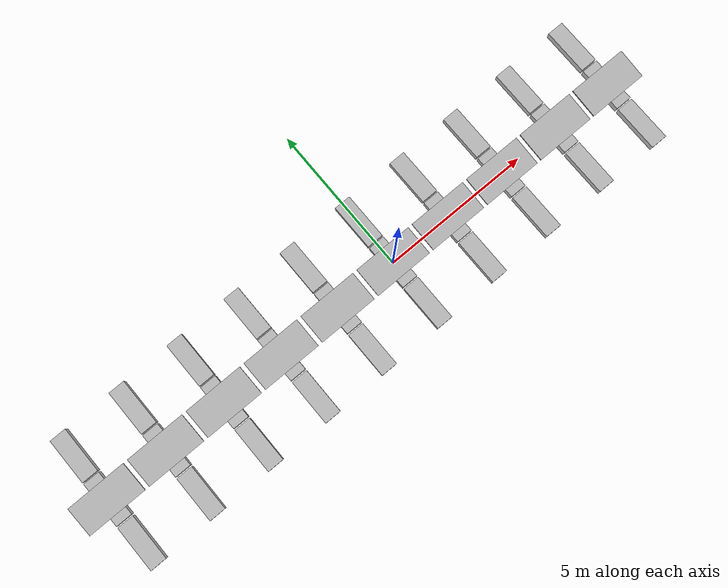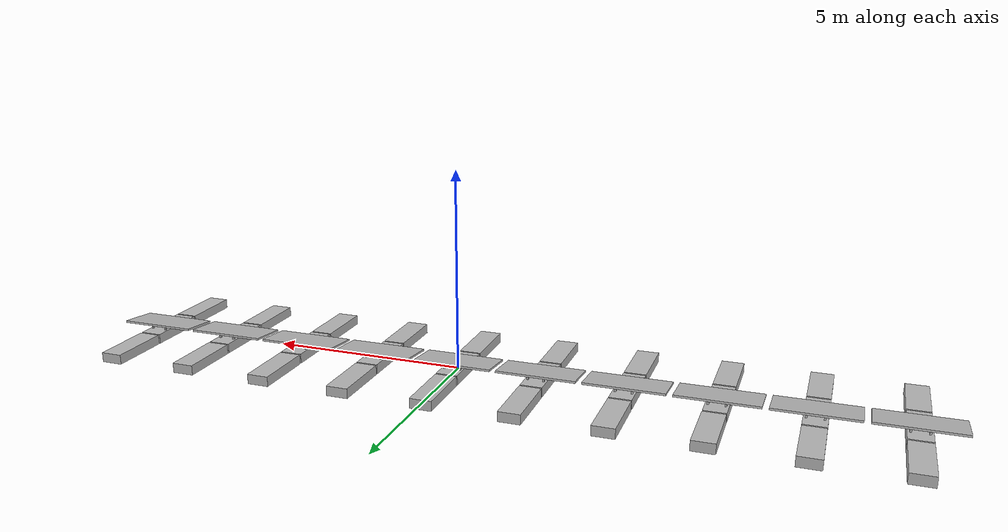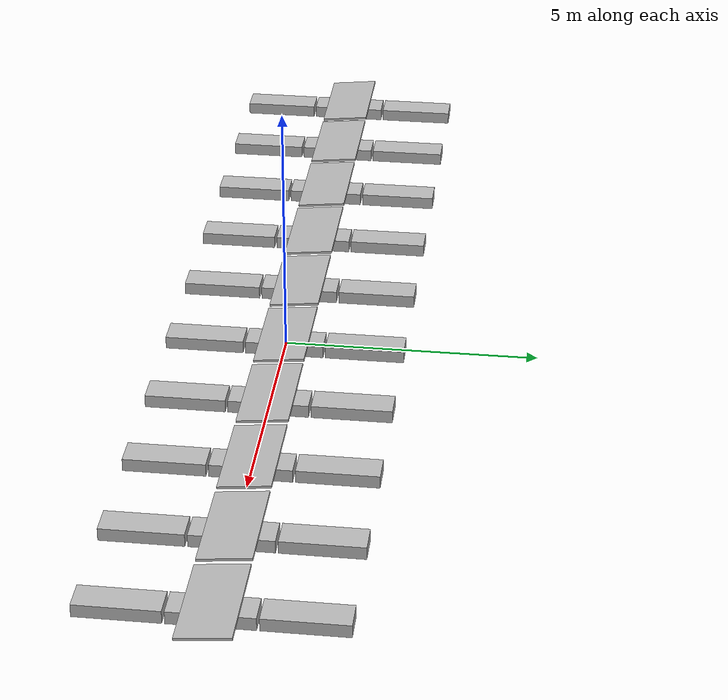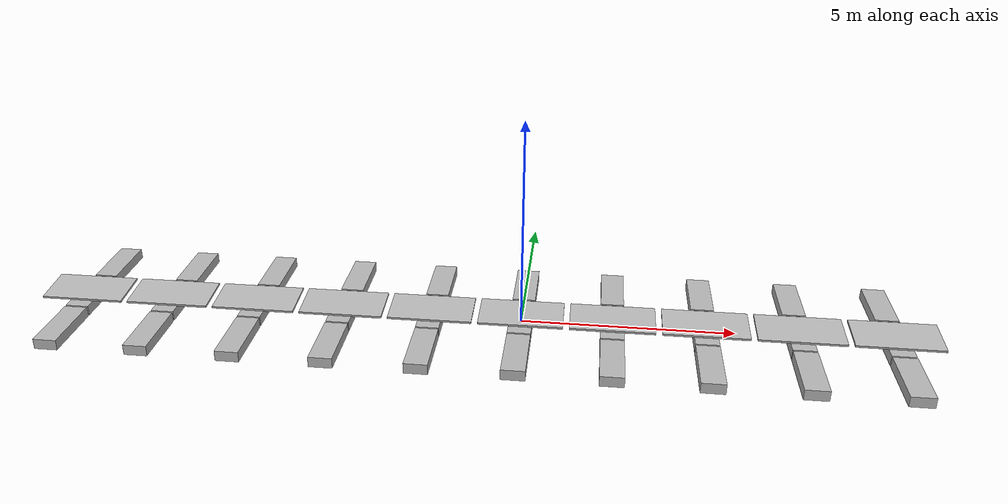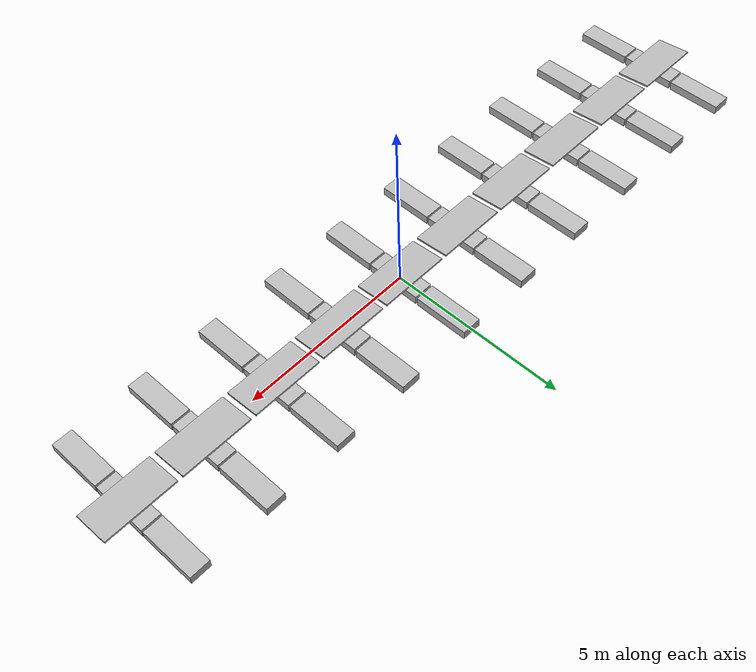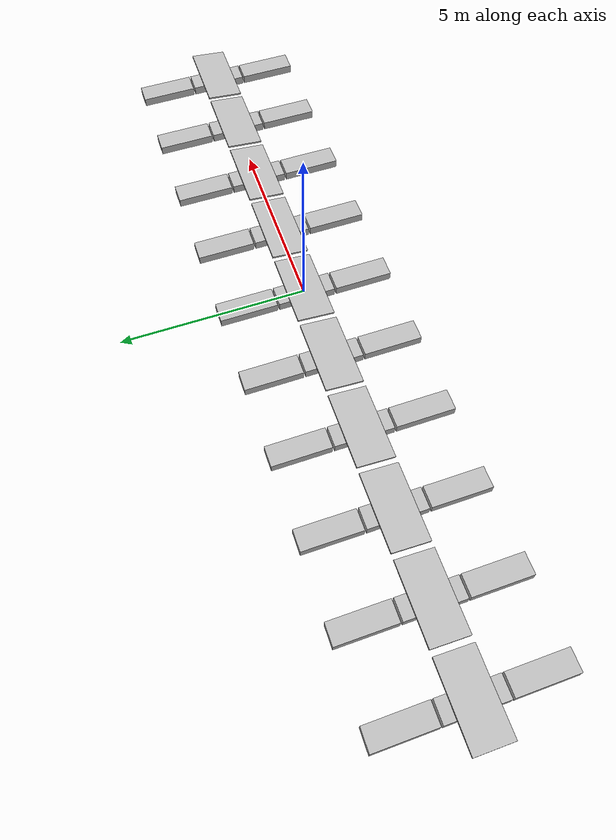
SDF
<?xml version="1.0" ?>
<sdf version="1.4">
  <world name="underwater">
    <include>
      <uri>model://sun</uri>
    </include>

    <include>
      <uri>model://test2</uri>
      <pose>0 0 0 0 0 0</pose>
    </include>

  </world>
</sdf>

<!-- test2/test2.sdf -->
<sdf version='1.5'>

  <model name='test2'>
    <plugin name="freebuoyancy_gazebo" filename="libfreebuoyancy_gazebo.so">
        <descriptionParam>robot_description</descriptionParam>
        <fluidTopic>current</fluidTopic>
        <alwaysOn>true</alwaysOn>
        <surface>0 0 0</surface>
        <updateRate>.001</updateRate>
    </plugin>

  <!-- Roll1 -->
      <link name='float_11'>
        <pose>-10.75 0 0 0 0 0</pose>
        <inertial>
          <mass>100</mass>
          <inertia>
            <ixx>20.541666</ixx>
            <ixy>0</ixy>
            <ixz>0</ixz>
            <iyy>3.041666</iyy>
            <iyz>0</iyz>
            <izz>22.541666</izz>
          </inertia>
        </inertial>

        <visual name='base_link_visual'>
          <geometry>
            <box>
              <size>0.55 1.55 0.25</size>
            </box>
          </geometry>
        </visual>

        <collision name='base_link_collision'>
          <geometry>
            <box>
              <size>0.55 1.55 0.25</size>
            </box>
          </geometry>
        </collision>

        <buoyancy>
          <compensation>2.00</compensation>
          <origin xyz= "0 0 0"/>
        </buoyancy>
      </link>

      <link name='float_12'>
        <pose>-10.75 1.6 0 0 0 0</pose>
        <inertial>
          <mass>100</mass>
          <inertia>
            <ixx>20.541666</ixx>
            <ixy>0</ixy>
            <ixz>0</ixz>
            <iyy>3.041666</iyy>
            <iyz>0</iyz>
            <izz>22.541666</izz>
          </inertia>
        </inertial>

        <visual name='base_link_visual'>
          <geometry>
            <box>
              <size>0.55 1.55 0.25</size>
            </box>
          </geometry>
        </visual>

        <collision name='base_link_collision'>
          <geometry>
            <box>
              <size>0.55 1.55 0.25</size>
            </box>
          </geometry>
        </collision>

        <buoyancy>
          <compensation>2.00</compensation>
          <origin xyz= "0 0 0"/>
        </buoyancy>
      </link>

      <link name='float_13'>
        <pose>-10.75 -1.6 0 0 0 0</pose>
        <inertial>
          <mass>100</mass>
          <inertia>
            <ixx>20.541666</ixx>
            <ixy>0</ixy>
            <ixz>0</ixz>
            <iyy>3.041666</iyy>
            <iyz>0</iyz>
            <izz>22.541666</izz>
          </inertia>
        </inertial>

        <visual name='base_link_visual'>
          <geometry>
            <box>
              <size>0.55 1.55 0.25</size>
            </box>
          </geometry>
        </visual>

        <collision name='base_link_collision'>
          <geometry>
            <box>
              <size>0.55 1.55 0.25</size>
            </box>
          </geometry>
        </collision>

        <buoyancy>
          <compensation>2.00</compensation>
          <origin xyz= "0 0 0"/>
        </buoyancy>
      </link>

      <joint name="joint11" type="prismatic">
        <parent>world</parent>
        <child>float_11</child>
        <pose>0 0 0 0 0 0</pose>
        <axis>
          <xyz>0 0 1</xyz>
        </axis>
      </joint>

      <joint name="joint12" type="prismatic">
        <parent>world</parent>
        <child>float_12</child>
        <pose>0 0 0 0 0 0</pose>
        <axis>
          <xyz>0 0 1</xyz>
        </axis>
      </joint>

      <joint name="joint13" type="prismatic">
        <parent>world</parent>
        <child>float_13</child>
        <pose>0 0 0 0 0 0</pose>
        <axis>
          <xyz>0 0 1</xyz>
        </axis>
      </joint>

      <link name='small_box_11'>
        <pose>-10.95 -0.4 0.075 0 0 0</pose>
        <inertial>
          <mass>0.001</mass>
          <inertia>
            <ixx>0.0000035</ixx>
            <ixy>0</ixy>
            <ixz>0</ixz>
            <iyy>0.0000035</iyy>
            <iyz>0</iyz>
            <izz>0.00000041</izz>
          </inertia>
        </inertial>
        <visual name='small_box_1_visual'>
          <geometry>
            <box>
              <size>0.05 0.05 0.15</size>
            </box>
          </geometry>
        </visual>
        <collision name='small_box_1_collision'>
          <geometry>
            <box>
              <size>0.05 0.05 0.15</size>
            </box>
          </geometry>
        </collision>
      </link>
      <joint name="small_box_11_joint" type="fixed">
        <parent>float_11</parent>
        <child>small_box_11</child>
      </joint>

      <!-- Small box 2 (front left pole, taller) -->
      <link name='small_box_12'>
        <pose>-10.95 0.4 0.15 0 0 0</pose> <!-- Adjusted Z position for height -->
        <inertial>
          <mass>0.001</mass>
          <inertia>
            <ixx>0.0000035</ixx>
            <ixy>0</ixy>
            <ixz>0</ixz>
            <iyy>0.0000035</iyy>
            <iyz>0</iyz>
            <izz>0.00000041</izz>
          </inertia>
        </inertial>
        <visual name='small_box_2_visual'>
          <geometry>
            <box>
              <size>0.05 0.05 0.20</size>
            </box>
          </geometry>
        </visual>
        <collision name='small_box_2_collision'>
          <geometry>
            <box>
              <size>0.05 0.05 0.20</size>
            </box>
          </geometry>
        </collision>
      </link>
      <joint name="small_box_12_joint" type="fixed">
        <parent>float_11</parent>
        <child>small_box_12</child>
      </joint>

      <!-- Small box 3 (rear right pole) -->
      <link name='small_box_13'>
        <pose>-10.55 -0.4 0.075 0 0 0</pose>
        <inertial>
          <mass>0.001</mass>
          <inertia>
            <ixx>0.0000035</ixx>
            <ixy>0</ixy>
            <ixz>0</ixz>
            <iyy>0.0000035</iyy>
            <iyz>0</iyz>
            <izz>0.00000041</izz>
          </inertia>
        </inertial>
        <visual name='small_box_3_visual'>
          <geometry>
            <box>
              <size>0.05 0.05 0.15</size>
            </box>
          </geometry>
        </visual>
        <collision name='small_box_3_collision'>
          <geometry>
            <box>
              <size>0.05 0.05 0.15</size>
            </box>
          </geometry>
        </collision>
      </link>
      <joint name="small_box_13_joint" type="fixed">
        <parent>float_11</parent>
        <child>small_box_13</child>
      </joint>

      <!-- Small box 4 (front right pole, taller) -->
      <link name='small_box_14'>
        <pose>-10.55 0.4 0.15 0 0 0</pose> <!-- Adjusted Z position for height -->
        <inertial>
          <mass>0.001</mass>
          <inertia>
            <ixx>0.0000035</ixx>
            <ixy>0</ixy>
            <ixz>0</ixz>
            <iyy>0.0000035</iyy>
            <iyz>0</iyz>
            <izz>0.00000041</izz>
          </inertia>
        </inertial>
        <visual name='small_box_4_visual'>
          <geometry>
            <box>
              <size>0.05 0.05 0.20</size>
            </box>
          </geometry>
        </visual>
        <collision name='small_box_4_collision'>
          <geometry>
            <box>
              <size>0.05 0.05 0.20</size>
            </box>
          </geometry>
        </collision>
      </link>
      <joint name="small_box_14_joint" type="fixed">
        <parent>float_11</parent>
        <child>small_box_14</child>
      </joint>

    <!-- Square -->
      <link name='top_square1'>
        <pose>-10.75 0 0.2 0.1 0 0</pose>
        <inertial>
          <pose>0 0 0 0 0 0</pose>
          <mass>0.001</mass>
          <inertia>
            <ixx>0.0000835</ixx>
            <ixy>0</ixy>
            <ixz>0</ixz>
            <iyy>0.000333</iyy>
            <iyz>0</iyz>
            <izz>0.000416</izz>
          </inertia>
        </inertial>
        <visual name='top_square_visual'>
          <geometry>
            <box>
              <size>2 1 0.05</size>
            </box>
          </geometry>
        </visual>
        <collision name='top_square_collision'>
          <geometry>
            <box>
              <size>2 1 0.05</size>
            </box>
          </geometry>
        </collision>
      </link>

      <!-- Fixed joints to attach the square platform to each pole -->
      <joint name="top_square_to_small_box_11" type="fixed">
        <parent>small_box_11</parent>
        <child>top_square1</child>
      </joint>

      <joint name="top_square_to_small_box_12" type="fixed">
        <parent>small_box_12</parent>
        <child>top_square1</child>
      </joint>

      <joint name="top_square_to_small_box_13" type="fixed">
        <parent>small_box_13</parent>
        <child>top_square1</child>
      </joint>

      <joint name="top_square_to_small_box_14" type="fixed">
        <parent>small_box_14</parent>
        <child>top_square1</child>
      </joint>

  <!-- Roll2 -->
      <link name='float_21'>
        <pose>-8.6 0 0 0 0 0</pose>
        <inertial>
          <mass>100</mass>
          <inertia>
            <ixx>20.541666</ixx>
            <ixy>0</ixy>
            <ixz>0</ixz>
            <iyy>3.041666</iyy>
            <iyz>0</iyz>
            <izz>22.541666</izz>
          </inertia>
        </inertial>

        <visual name='base_link_visual'>
          <geometry>
            <box>
              <size>0.55 1.55 0.25</size>
            </box>
          </geometry>
        </visual>

        <collision name='base_link_collision'>
          <geometry>
            <box>
              <size>0.55 1.55 0.25</size>
            </box>
          </geometry>
        </collision>

        <buoyancy>
          <compensation>2.00</compensation>
          <origin xyz= "0 0 0"/>
        </buoyancy>
      </link>

      <link name='float_22'>
        <pose>-8.6 1.6 0 0 0 0</pose>
        <inertial>
          <mass>100</mass>
          <inertia>
            <ixx>20.541666</ixx>
            <ixy>0</ixy>
            <ixz>0</ixz>
            <iyy>3.041666</iyy>
            <iyz>0</iyz>
            <izz>22.541666</izz>
          </inertia>
        </inertial>

        <visual name='base_link_visual'>
          <geometry>
            <box>
              <size>0.55 1.55 0.25</size>
            </box>
          </geometry>
        </visual>

        <collision name='base_link_collision'>
          <geometry>
            <box>
              <size>0.55 1.55 0.25</size>
            </box>
          </geometry>
        </collision>

        <buoyancy>
          <compensation>2.00</compensation>
          <origin xyz= "0 0 0"/>
        </buoyancy>
      </link>

      <link name='float_23'>
        <pose>-8.6 -1.6 0 0 0 0</pose>
        <inertial>
          <mass>100</mass>
          <inertia>
            <ixx>20.541666</ixx>
            <ixy>0</ixy>
            <ixz>0</ixz>
            <iyy>3.041666</iyy>
            <iyz>0</iyz>
            <izz>22.541666</izz>
          </inertia>
        </inertial>

        <visual name='base_link_visual'>
          <geometry>
            <box>
              <size>0.55 1.55 0.25</size>
            </box>
          </geometry>
        </visual>

        <collision name='base_link_collision'>
          <geometry>
            <box>
              <size>0.55 1.55 0.25</size>
            </box>
          </geometry>
        </collision>

        <buoyancy>
          <compensation>2.00</compensation>
          <origin xyz= "0 0 0"/>
        </buoyancy>
      </link>

      <joint name="joint21" type="prismatic">
        <parent>world</parent>
        <child>float_21</child>
        <pose>0 0 0 0 0 0</pose>
        <axis>
          <xyz>0 0 1</xyz>
        </axis>
      </joint>

      <joint name="joint22" type="prismatic">
        <parent>world</parent>
        <child>float_22</child>
        <pose>0 0 0 0 0 0</pose>
        <axis>
          <xyz>0 0 1</xyz>
        </axis>
      </joint>

      <joint name="joint23" type="prismatic">
        <parent>world</parent>
        <child>float_23</child>
        <pose>0 0 0 0 0 0</pose>
        <axis>
          <xyz>0 0 1</xyz>
        </axis>
      </joint>

      <link name='small_box_21'>
        <pose>-8.8 -0.4 0.075 0 0 0</pose>
        <inertial>
          <mass>0.001</mass>
          <inertia>
            <ixx>0.0000035</ixx>
            <ixy>0</ixy>
            <ixz>0</ixz>
            <iyy>0.0000035</iyy>
            <iyz>0</iyz>
            <izz>0.00000041</izz>
          </inertia>
        </inertial>
        <visual name='small_box_1_visual'>
          <geometry>
            <box>
              <size>0.05 0.05 0.15</size>
            </box>
          </geometry>
        </visual>
        <collision name='small_box_1_collision'>
          <geometry>
            <box>
              <size>0.05 0.05 0.15</size>
            </box>
          </geometry>
        </collision>
      </link>
      <joint name="small_box_21_joint" type="fixed">
        <parent>float_21</parent>
        <child>small_box_21</child>
      </joint>

      <!-- Small box 2 (front left pole, taller) -->
      <link name='small_box_22'>
        <pose>-8.8 0.4 0.15 0 0 0</pose> <!-- Adjusted Z position for height -->
        <inertial>
          <mass>0.001</mass>
          <inertia>
            <ixx>0.0000035</ixx>
            <ixy>0</ixy>
            <ixz>0</ixz>
            <iyy>0.0000035</iyy>
            <iyz>0</iyz>
            <izz>0.00000041</izz>
          </inertia>
        </inertial>
        <visual name='small_box_2_visual'>
          <geometry>
            <box>
              <size>0.05 0.05 0.20</size>
            </box>
          </geometry>
        </visual>
        <collision name='small_box_2_collision'>
          <geometry>
            <box>
              <size>0.05 0.05 0.20</size>
            </box>
          </geometry>
        </collision>
      </link>
      <joint name="small_box_22_joint" type="fixed">
        <parent>float_21</parent>
        <child>small_box_22</child>
      </joint>

      <!-- Small box 3 (rear right pole) -->
      <link name='small_box_23'>
        <pose>-8.4 -0.4 0.075 0 0 0</pose>
        <inertial>
          <mass>0.001</mass>
          <inertia>
            <ixx>0.0000035</ixx>
            <ixy>0</ixy>
            <ixz>0</ixz>
            <iyy>0.0000035</iyy>
            <iyz>0</iyz>
            <izz>0.00000041</izz>
          </inertia>
        </inertial>
        <visual name='small_box_3_visual'>
          <geometry>
            <box>
              <size>0.05 0.05 0.15</size>
            </box>
          </geometry>
        </visual>
        <collision name='small_box_3_collision'>
          <geometry>
            <box>
              <size>0.05 0.05 0.15</size>
            </box>
          </geometry>
        </collision>
      </link>
      <joint name="small_box_23_joint" type="fixed">
        <parent>float_21</parent>
        <child>small_box_23</child>
      </joint>

      <!-- Small box 4 (front right pole, taller) -->
      <link name='small_box_24'>
        <pose>-8.4 0.4 0.15 0 0 0</pose> <!-- Adjusted Z position for height -->
        <inertial>
          <mass>0.001</mass>
          <inertia>
            <ixx>0.0000035</ixx>
            <ixy>0</ixy>
            <ixz>0</ixz>
            <iyy>0.0000035</iyy>
            <iyz>0</iyz>
            <izz>0.00000041</izz>
          </inertia>
        </inertial>
        <visual name='small_box_4_visual'>
          <geometry>
            <box>
              <size>0.05 0.05 0.20</size>
            </box>
          </geometry>
        </visual>
        <collision name='small_box_4_collision'>
          <geometry>
            <box>
              <size>0.05 0.05 0.20</size>
            </box>
          </geometry>
        </collision>
      </link>
      <joint name="small_box_24_joint" type="fixed">
        <parent>float_21</parent>
        <child>small_box_24</child>
      </joint>

    <!-- Square -->
      <link name='top_square2'>
        <pose>-8.6 0 0.2 0.1 0 0</pose>
        <inertial>
          <pose>0 0 0 0 0 0</pose>
          <mass>0.001</mass>
          <inertia>
            <ixx>0.0000835</ixx>
            <ixy>0</ixy>
            <ixz>0</ixz>
            <iyy>0.000333</iyy>
            <iyz>0</iyz>
            <izz>0.000416</izz>
          </inertia>
        </inertial>
        <visual name='top_square_visual'>
          <geometry>
            <box>
              <size>2 1 0.05</size>
            </box>
          </geometry>
        </visual>
        <collision name='top_square_collision'>
          <geometry>
            <box>
              <size>2 1 0.05</size>
            </box>
          </geometry>
        </collision>
      </link>

      <!-- Fixed joints to attach the square platform to each pole -->
      <joint name="top_square_to_small_box_21" type="fixed">
        <parent>small_box_21</parent>
        <child>top_square2</child>
      </joint>

      <joint name="top_square_to_small_box_22" type="fixed">
        <parent>small_box_22</parent>
        <child>top_square2</child>
      </joint>

      <joint name="top_square_to_small_box_23" type="fixed">
        <parent>small_box_23</parent>
        <child>top_square2</child>
      </joint>

      <joint name="top_square_to_small_box_24" type="fixed">
        <parent>small_box_24</parent>
        <child>top_square2</child>
      </joint>

  <!-- Roll3 -->
      <link name='float_31'>
        <pose>-6.45 0 0 0 0 0</pose>
        <inertial>
          <mass>100</mass>
          <inertia>
            <ixx>20.541666</ixx>
            <ixy>0</ixy>
            <ixz>0</ixz>
            <iyy>3.041666</iyy>
            <iyz>0</iyz>
            <izz>22.541666</izz>
          </inertia>
        </inertial>

        <visual name='base_link_visual'>
          <geometry>
            <box>
              <size>0.55 1.55 0.25</size>
            </box>
          </geometry>
        </visual>

        <collision name='base_link_collision'>
          <geometry>
            <box>
              <size>0.55 1.55 0.25</size>
            </box>
          </geometry>
        </collision>

        <buoyancy>
          <compensation>2.00</compensation>
          <origin xyz= "0 0 0"/>
        </buoyancy>
      </link>

      <link name='float_32'>
        <pose>-6.45 1.6 0 0 0 0</pose>
        <inertial>
          <mass>100</mass>
          <inertia>
            <ixx>20.541666</ixx>
            <ixy>0</ixy>
            <ixz>0</ixz>
            <iyy>3.041666</iyy>
            <iyz>0</iyz>
            <izz>22.541666</izz>
          </inertia>
        </inertial>

        <visual name='base_link_visual'>
          <geometry>
            <box>
              <size>0.55 1.55 0.25</size>
            </box>
          </geometry>
        </visual>

        <collision name='base_link_collision'>
          <geometry>
            <box>
              <size>0.55 1.55 0.25</size>
            </box>
          </geometry>
        </collision>

        <buoyancy>
          <compensation>2.00</compensation>
          <origin xyz= "0 0 0"/>
        </buoyancy>
      </link>

      <link name='float_33'>
        <pose>-6.45 -1.6 0 0 0 0</pose>
        <inertial>
          <mass>100</mass>
          <inertia>
            <ixx>20.541666</ixx>
            <ixy>0</ixy>
            <ixz>0</ixz>
            <iyy>3.041666</iyy>
            <iyz>0</iyz>
            <izz>22.541666</izz>
          </inertia>
        </inertial>

        <visual name='base_link_visual'>
          <geometry>
            <box>
              <size>0.55 1.55 0.25</size>
            </box>
          </geometry>
        </visual>

        <collision name='base_link_collision'>
          <geometry>
            <box>
              <size>0.55 1.55 0.25</size>
            </box>
          </geometry>
        </collision>

        <buoyancy>
          <compensation>2.00</compensation>
          <origin xyz= "0 0 0"/>
        </buoyancy>
      </link>

      <joint name="joint31" type="prismatic">
        <parent>world</parent>
        <child>float_31</child>
        <pose>0 0 0 0 0 0</pose>
        <axis>
          <xyz>0 0 1</xyz>
        </axis>
      </joint>

      <joint name="joint32" type="prismatic">
        <parent>world</parent>
        <child>float_32</child>
        <pose>0 0 0 0 0 0</pose>
        <axis>
          <xyz>0 0 1</xyz>
        </axis>
      </joint>

      <joint name="joint33" type="prismatic">
        <parent>world</parent>
        <child>float_33</child>
        <pose>0 0 0 0 0 0</pose>
        <axis>
          <xyz>0 0 1</xyz>
        </axis>
      </joint>

      <link name='small_box_31'>
        <pose>-6.65 -0.4 0.075 0 0 0</pose>
        <inertial>
          <mass>0.001</mass>
          <inertia>
            <ixx>0.0000035</ixx>
            <ixy>0</ixy>
            <ixz>0</ixz>
            <iyy>0.0000035</iyy>
            <iyz>0</iyz>
            <izz>0.00000041</izz>
          </inertia>
        </inertial>
        <visual name='small_box_1_visual'>
          <geometry>
            <box>
              <size>0.05 0.05 0.15</size>
            </box>
          </geometry>
        </visual>
        <collision name='small_box_1_collision'>
          <geometry>
            <box>
              <size>0.05 0.05 0.15</size>
            </box>
          </geometry>
        </collision>
      </link>
      <joint name="small_box_31_joint" type="fixed">
        <parent>float_31</parent>
        <child>small_box_31</child>
      </joint>

      <!-- Small box 2 (front left pole, taller) -->
      <link name='small_box_32'>
        <pose>-6.65 0.4 0.15 0 0 0</pose> <!-- Adjusted Z position for height -->
        <inertial>
          <mass>0.001</mass>
          <inertia>
            <ixx>0.0000035</ixx>
            <ixy>0</ixy>
            <ixz>0</ixz>
            <iyy>0.0000035</iyy>
            <iyz>0</iyz>
            <izz>0.00000041</izz>
          </inertia>
        </inertial>
        <visual name='small_box_2_visual'>
          <geometry>
            <box>
              <size>0.05 0.05 0.20</size>
            </box>
          </geometry>
        </visual>
        <collision name='small_box_2_collision'>
          <geometry>
            <box>
              <size>0.05 0.05 0.20</size>
            </box>
          </geometry>
        </collision>
      </link>
      <joint name="small_box_32_joint" type="fixed">
        <parent>float_31</parent>
        <child>small_box_32</child>
      </joint>

      <!-- Small box 3 (rear right pole) -->
      <link name='small_box_33'>
        <pose>-6.25 -0.4 0.075 0 0 0</pose>
        <inertial>
          <mass>0.001</mass>
          <inertia>
            <ixx>0.0000035</ixx>
            <ixy>0</ixy>
            <ixz>0</ixz>
            <iyy>0.0000035</iyy>
            <iyz>0</iyz>
            <izz>0.00000041</izz>
          </inertia>
        </inertial>
        <visual name='small_box_3_visual'>
          <geometry>
            <box>
              <size>0.05 0.05 0.15</size>
            </box>
          </geometry>
        </visual>
        <collision name='small_box_3_collision'>
          <geometry>
            <box>
              <size>0.05 0.05 0.15</size>
            </box>
          </geometry>
        </collision>
      </link>
      <joint name="small_box_33_joint" type="fixed">
        <parent>float_31</parent>
        <child>small_box_33</child>
      </joint>

      <!-- Small box 4 (front right pole, taller) -->
      <link name='small_box_34'>
        <pose>-6.25 0.4 0.15 0 0 0</pose> <!-- Adjusted Z position for height -->
        <inertial>
          <mass>0.001</mass>
          <inertia>
            <ixx>0.0000035</ixx>
            <ixy>0</ixy>
            <ixz>0</ixz>
            <iyy>0.0000035</iyy>
            <iyz>0</iyz>
            <izz>0.00000041</izz>
          </inertia>
        </inertial>
        <visual name='small_box_4_visual'>
          <geometry>
            <box>
              <size>0.05 0.05 0.20</size>
            </box>
          </geometry>
        </visual>
        <collision name='small_box_4_collision'>
          <geometry>
            <box>
              <size>0.05 0.05 0.20</size>
            </box>
          </geometry>
        </collision>
      </link>
      <joint name="small_box_34_joint" type="fixed">
        <parent>float_31</parent>
        <child>small_box_34</child>
      </joint>

    <!-- Square -->
      <link name='top_square3'>
        <pose>-6.45 0 0.2 0.1 0 0</pose>
        <inertial>
          <pose>0 0 0 0 0 0</pose>
          <mass>0.001</mass>
          <inertia>
            <ixx>0.0000835</ixx>
            <ixy>0</ixy>
            <ixz>0</ixz>
            <iyy>0.000333</iyy>
            <iyz>0</iyz>
            <izz>0.000416</izz>
          </inertia>
        </inertial>
        <visual name='top_square_visual'>
          <geometry>
            <box>
              <size>2 1 0.05</size>
            </box>
          </geometry>
        </visual>
        <collision name='top_square_collision'>
          <geometry>
            <box>
              <size>2 1 0.05</size>
            </box>
          </geometry>
        </collision>
      </link>

      <!-- Fixed joints to attach the square platform to each pole -->
      <joint name="top_square_to_small_box_31" type="fixed">
        <parent>small_box_31</parent>
        <child>top_square3</child>
      </joint>

      <joint name="top_square_to_small_box_32" type="fixed">
        <parent>small_box_32</parent>
        <child>top_square3</child>
      </joint>

      <joint name="top_square_to_small_box_33" type="fixed">
        <parent>small_box_33</parent>
        <child>top_square3</child>
      </joint>

      <joint name="top_square_to_small_box_34" type="fixed">
        <parent>small_box_34</parent>
        <child>top_square3</child>
      </joint>

  <!-- Roll4 -->
      <link name='float_41'>
        <pose>-4.3 0 0 0 0 0</pose>
        <inertial>
          <mass>100</mass>
          <inertia>
            <ixx>20.541666</ixx>
            <ixy>0</ixy>
            <ixz>0</ixz>
            <iyy>3.041666</iyy>
            <iyz>0</iyz>
            <izz>22.541666</izz>
          </inertia>
        </inertial>

        <visual name='base_link_visual'>
          <geometry>
            <box>
              <size>0.55 1.55 0.25</size>
            </box>
          </geometry>
        </visual>

        <collision name='base_link_collision'>
          <geometry>
            <box>
              <size>0.55 1.55 0.25</size>
            </box>
          </geometry>
        </collision>

        <buoyancy>
          <compensation>2.00</compensation>
          <origin xyz= "0 0 0"/>
        </buoyancy>
      </link>

      <link name='float_42'>
        <pose>-4.3 1.6 0 0 0 0</pose>
        <inertial>
          <mass>100</mass>
          <inertia>
            <ixx>20.541666</ixx>
            <ixy>0</ixy>
            <ixz>0</ixz>
            <iyy>3.041666</iyy>
            <iyz>0</iyz>
            <izz>22.541666</izz>
          </inertia>
        </inertial>

        <visual name='base_link_visual'>
          <geometry>
            <box>
              <size>0.55 1.55 0.25</size>
            </box>
          </geometry>
        </visual>

        <collision name='base_link_collision'>
          <geometry>
            <box>
              <size>0.55 1.55 0.25</size>
            </box>
          </geometry>
        </collision>

        <buoyancy>
          <compensation>2.00</compensation>
          <origin xyz= "0 0 0"/>
        </buoyancy>
      </link>

      <link name='float_43'>
        <pose>-4.3 -1.6 0 0 0 0</pose>
        <inertial>
          <mass>100</mass>
          <inertia>
            <ixx>20.541666</ixx>
            <ixy>0</ixy>
            <ixz>0</ixz>
            <iyy>3.041666</iyy>
            <iyz>0</iyz>
            <izz>22.541666</izz>
          </inertia>
        </inertial>

        <visual name='base_link_visual'>
          <geometry>
            <box>
              <size>0.55 1.55 0.25</size>
            </box>
          </geometry>
        </visual>

        <collision name='base_link_collision'>
          <geometry>
            <box>
              <size>0.55 1.55 0.25</size>
            </box>
          </geometry>
        </collision>

        <buoyancy>
          <compensation>2.00</compensation>
          <origin xyz= "0 0 0"/>
        </buoyancy>
      </link>

      <joint name="joint41" type="prismatic">
        <parent>world</parent>
        <child>float_41</child>
        <pose>0 0 0 0 0 0</pose>
        <axis>
          <xyz>0 0 1</xyz>
        </axis>
      </joint>

      <joint name="joint42" type="prismatic">
        <parent>world</parent>
        <child>float_42</child>
        <pose>0 0 0 0 0 0</pose>
        <axis>
          <xyz>0 0 1</xyz>
        </axis>
      </joint>

      <joint name="joint43" type="prismatic">
        <parent>world</parent>
        <child>float_43</child>
        <pose>0 0 0 0 0 0</pose>
        <axis>
          <xyz>0 0 1</xyz>
        </axis>
      </joint>

      <link name='small_box_41'>
        <pose>-4.5 -0.4 0.075 0 0 0</pose>
        <inertial>
          <mass>0.001</mass>
          <inertia>
            <ixx>0.0000035</ixx>
            <ixy>0</ixy>
            <ixz>0</ixz>
            <iyy>0.0000035</iyy>
            <iyz>0</iyz>
            <izz>0.00000041</izz>
          </inertia>
        </inertial>
        <visual name='small_box_1_visual'>
          <geometry>
            <box>
              <size>0.05 0.05 0.15</size>
            </box>
          </geometry>
        </visual>
        <collision name='small_box_1_collision'>
          <geometry>
            <box>
              <size>0.05 0.05 0.15</size>
            </box>
          </geometry>
        </collision>
      </link>
      <joint name="small_box_41_joint" type="fixed">
        <parent>float_41</parent>
        <child>small_box_41</child>
      </joint>

      <!-- Small box 2 (front left pole, taller) -->
      <link name='small_box_42'>
        <pose>-4.5 0.4 0.15 0 0 0</pose> <!-- Adjusted Z position for height -->
        <inertial>
          <mass>0.001</mass>
          <inertia>
            <ixx>0.0000035</ixx>
            <ixy>0</ixy>
            <ixz>0</ixz>
            <iyy>0.0000035</iyy>
            <iyz>0</iyz>
            <izz>0.00000041</izz>
          </inertia>
        </inertial>
        <visual name='small_box_2_visual'>
          <geometry>
            <box>
              <size>0.05 0.05 0.20</size>
            </box>
          </geometry>
        </visual>
        <collision name='small_box_2_collision'>
          <geometry>
            <box>
              <size>0.05 0.05 0.20</size>
            </box>
          </geometry>
        </collision>
      </link>
      <joint name="small_box_42_joint" type="fixed">
        <parent>float_41</parent>
        <child>small_box_42</child>
      </joint>

      <!-- Small box 3 (rear right pole) -->
      <link name='small_box_43'>
        <pose>-4.1 -0.4 0.075 0 0 0</pose>
        <inertial>
          <mass>0.001</mass>
          <inertia>
            <ixx>0.0000035</ixx>
            <ixy>0</ixy>
            <ixz>0</ixz>
            <iyy>0.0000035</iyy>
            <iyz>0</iyz>
            <izz>0.00000041</izz>
          </inertia>
        </inertial>
        <visual name='small_box_3_visual'>
          <geometry>
            <box>
              <size>0.05 0.05 0.15</size>
            </box>
          </geometry>
        </visual>
        <collision name='small_box_3_collision'>
          <geometry>
            <box>
              <size>0.05 0.05 0.15</size>
            </box>
          </geometry>
        </collision>
      </link>
      <joint name="small_box_43_joint" type="fixed">
        <parent>float_41</parent>
        <child>small_box_43</child>
      </joint>

      <!-- Small box 4 (front right pole, taller) -->
      <link name='small_box_44'>
        <pose>-4.1 0.4 0.15 0 0 0</pose> <!-- Adjusted Z position for height -->
        <inertial>
          <mass>0.001</mass>
          <inertia>
            <ixx>0.0000035</ixx>
            <ixy>0</ixy>
            <ixz>0</ixz>
            <iyy>0.0000035</iyy>
            <iyz>0</iyz>
            <izz>0.00000041</izz>
          </inertia>
        </inertial>
        <visual name='small_box_4_visual'>
          <geometry>
            <box>
              <size>0.05 0.05 0.20</size>
            </box>
          </geometry>
        </visual>
        <collision name='small_box_4_collision'>
          <geometry>
            <box>
              <size>0.05 0.05 0.20</size>
            </box>
          </geometry>
        </collision>
      </link>
      <joint name="small_box_44_joint" type="fixed">
        <parent>float_41</parent>
        <child>small_box_44</child>
      </joint>

    <!-- Square -->
      <link name='top_square4'>
        <pose>-4.3 0 0.2 0.1 0 0</pose>
        <inertial>
          <pose>0 0 0 0 0 0</pose>
          <mass>0.001</mass>
          <inertia>
            <ixx>0.0000835</ixx>
            <ixy>0</ixy>
            <ixz>0</ixz>
            <iyy>0.000333</iyy>
            <iyz>0</iyz>
            <izz>0.000416</izz>
          </inertia>
        </inertial>
        <visual name='top_square_visual'>
          <geometry>
            <box>
              <size>2 1 0.05</size>
            </box>
          </geometry>
        </visual>
        <collision name='top_square_collision'>
          <geometry>
            <box>
              <size>2 1 0.05</size>
            </box>
          </geometry>
        </collision>
      </link>

      <!-- Fixed joints to attach the square platform to each pole -->
      <joint name="top_square_to_small_box_41" type="fixed">
        <parent>small_box_41</parent>
        <child>top_square4</child>
      </joint>

      <joint name="top_square_to_small_box_42" type="fixed">
        <parent>small_box_42</parent>
        <child>top_square4</child>
      </joint>

      <joint name="top_square_to_small_box_43" type="fixed">
        <parent>small_box_43</parent>
        <child>top_square4</child>
      </joint>

      <joint name="top_square_to_small_box_44" type="fixed">
        <parent>small_box_44</parent>
        <child>top_square4</child>
      </joint>

  <!-- Roll5 -->
      <link name='float_51'>
        <pose>-2.15 0 0 0 0 0</pose>
        <inertial>
          <mass>100</mass>
          <inertia>
            <ixx>20.541666</ixx>
            <ixy>0</ixy>
            <ixz>0</ixz>
            <iyy>3.041666</iyy>
            <iyz>0</iyz>
            <izz>22.541666</izz>
          </inertia>
        </inertial>

        <visual name='base_link_visual'>
          <geometry>
            <box>
              <size>0.55 1.55 0.25</size>
            </box>
          </geometry>
        </visual>

        <collision name='base_link_collision'>
          <geometry>
            <box>
              <size>0.55 1.55 0.25</size>
            </box>
          </geometry>
        </collision>

        <buoyancy>
          <compensation>2.00</compensation>
          <origin xyz= "0 0 0"/>
        </buoyancy>
      </link>

      <link name='float_52'>
        <pose>-2.15 1.6 0 0 0 0</pose>
        <inertial>
          <mass>100</mass>
          <inertia>
            <ixx>20.541666</ixx>
            <ixy>0</ixy>
            <ixz>0</ixz>
            <iyy>3.041666</iyy>
            <iyz>0</iyz>
            <izz>22.541666</izz>
          </inertia>
        </inertial>

        <visual name='base_link_visual'>
          <geometry>
            <box>
              <size>0.55 1.55 0.25</size>
            </box>
          </geometry>
        </visual>

        <collision name='base_link_collision'>
          <geometry>
            <box>
              <size>0.55 1.55 0.25</size>
            </box>
          </geometry>
        </collision>

        <buoyancy>
          <compensation>2.00</compensation>
          <origin xyz= "0 0 0"/>
        </buoyancy>
      </link>

      <link name='float_53'>
        <pose>-2.15 -1.6 0 0 0 0</pose>
        <inertial>
          <mass>100</mass>
          <inertia>
            <ixx>20.541666</ixx>
            <ixy>0</ixy>
            <ixz>0</ixz>
            <iyy>3.041666</iyy>
            <iyz>0</iyz>
            <izz>22.541666</izz>
          </inertia>
        </inertial>

        <visual name='base_link_visual'>
          <geometry>
            <box>
              <size>0.55 1.55 0.25</size>
            </box>
          </geometry>
        </visual>

        <collision name='base_link_collision'>
          <geometry>
            <box>
              <size>0.55 1.55 0.25</size>
            </box>
          </geometry>
        </collision>

        <buoyancy>
          <compensation>2.00</compensation>
          <origin xyz= "0 0 0"/>
        </buoyancy>
      </link>

      <joint name="joint51" type="prismatic">
        <parent>world</parent>
        <child>float_51</child>
        <pose>0 0 0 0 0 0</pose>
        <axis>
          <xyz>0 0 1</xyz>
        </axis>
      </joint>

      <joint name="joint52" type="prismatic">
        <parent>world</parent>
        <child>float_52</child>
        <pose>0 0 0 0 0 0</pose>
        <axis>
          <xyz>0 0 1</xyz>
        </axis>
      </joint>

      <joint name="joint53" type="prismatic">
        <parent>world</parent>
        <child>float_53</child>
        <pose>0 0 0 0 0 0</pose>
        <axis>
          <xyz>0 0 1</xyz>
        </axis>
      </joint>

      <link name='small_box_51'>
        <pose>-2.35 -0.4 0.075 0 0 0</pose>
        <inertial>
          <mass>0.001</mass>
          <inertia>
            <ixx>0.0000035</ixx>
            <ixy>0</ixy>
            <ixz>0</ixz>
            <iyy>0.0000035</iyy>
            <iyz>0</iyz>
            <izz>0.00000041</izz>
          </inertia>
        </inertial>
        <visual name='small_box_1_visual'>
          <geometry>
            <box>
              <size>0.05 0.05 0.15</size>
            </box>
          </geometry>
        </visual>
        <collision name='small_box_1_collision'>
          <geometry>
            <box>
              <size>0.05 0.05 0.15</size>
            </box>
          </geometry>
        </collision>
      </link>
      <joint name="small_box_51_joint" type="fixed">
        <parent>float_51</parent>
        <child>small_box_51</child>
      </joint>

      <!-- Small box 2 (front left pole, taller) -->
      <link name='small_box_52'>
        <pose>-2.35 0.4 0.15 0 0 0</pose> <!-- Adjusted Z position for height -->
        <inertial>
          <mass>0.001</mass>
          <inertia>
            <ixx>0.0000035</ixx>
            <ixy>0</ixy>
            <ixz>0</ixz>
            <iyy>0.0000035</iyy>
            <iyz>0</iyz>
            <izz>0.00000041</izz>
          </inertia>
        </inertial>
        <visual name='small_box_2_visual'>
          <geometry>
            <box>
              <size>0.05 0.05 0.20</size>
            </box>
          </geometry>
        </visual>
        <collision name='small_box_2_collision'>
          <geometry>
            <box>
              <size>0.05 0.05 0.20</size>
            </box>
          </geometry>
        </collision>
      </link>
      <joint name="small_box_52_joint" type="fixed">
        <parent>float_51</parent>
        <child>small_box_52</child>
      </joint>

      <!-- Small box 3 (rear right pole) -->
      <link name='small_box_53'>
        <pose>-1.95 -0.4 0.075 0 0 0</pose>
        <inertial>
          <mass>0.001</mass>
          <inertia>
            <ixx>0.0000035</ixx>
            <ixy>0</ixy>
            <ixz>0</ixz>
            <iyy>0.0000035</iyy>
            <iyz>0</iyz>
            <izz>0.00000041</izz>
          </inertia>
        </inertial>
        <visual name='small_box_3_visual'>
          <geometry>
            <box>
              <size>0.05 0.05 0.15</size>
            </box>
          </geometry>
        </visual>
        <collision name='small_box_3_collision'>
          <geometry>
            <box>
              <size>0.05 0.05 0.15</size>
            </box>
          </geometry>
        </collision>
      </link>
      <joint name="small_box_53_joint" type="fixed">
        <parent>float_51</parent>
        <child>small_box_53</child>
      </joint>

      <!-- Small box 4 (front right pole, taller) -->
      <link name='small_box_54'>
        <pose>-1.95 0.4 0.15 0 0 0</pose> <!-- Adjusted Z position for height -->
        <inertial>
          <mass>0.001</mass>
          <inertia>
            <ixx>0.0000035</ixx>
            <ixy>0</ixy>
            <ixz>0</ixz>
            <iyy>0.0000035</iyy>
            <iyz>0</iyz>
            <izz>0.00000041</izz>
          </inertia>
        </inertial>
        <visual name='small_box_4_visual'>
          <geometry>
            <box>
              <size>0.05 0.05 0.20</size>
            </box>
          </geometry>
        </visual>
        <collision name='small_box_4_collision'>
          <geometry>
            <box>
              <size>0.05 0.05 0.20</size>
            </box>
          </geometry>
        </collision>
      </link>
      <joint name="small_box_54_joint" type="fixed">
        <parent>float_51</parent>
        <child>small_box_54</child>
      </joint>

    <!-- Square -->
      <link name='top_square5'>
        <pose>-2.15 0 0.2 0.1 0 0</pose>
        <inertial>
          <pose>0 0 0 0 0 0</pose>
          <mass>0.001</mass>
          <inertia>
            <ixx>0.0000835</ixx>
            <ixy>0</ixy>
            <ixz>0</ixz>
            <iyy>0.000333</iyy>
            <iyz>0</iyz>
            <izz>0.000416</izz>
          </inertia>
        </inertial>
        <visual name='top_square_visual'>
          <geometry>
            <box>
              <size>2 1 0.05</size>
            </box>
          </geometry>
        </visual>
        <collision name='top_square_collision'>
          <geometry>
            <box>
              <size>2 1 0.05</size>
            </box>
          </geometry>
        </collision>
      </link>

      <!-- Fixed joints to attach the square platform to each pole -->
      <joint name="top_square_to_small_box_51" type="fixed">
        <parent>small_box_51</parent>
        <child>top_square5</child>
      </joint>

      <joint name="top_square_to_small_box_52" type="fixed">
        <parent>small_box_52</parent>
        <child>top_square5</child>
      </joint>

      <joint name="top_square_to_small_box_53" type="fixed">
        <parent>small_box_53</parent>
        <child>top_square5</child>
      </joint>

      <joint name="top_square_to_small_box_54" type="fixed">
        <parent>small_box_54</parent>
        <child>top_square5</child>
      </joint>

  <!-- Roll6 -->
      <link name='float_61'>
        <pose>0 0 0 0 0 0</pose>
        <inertial>
          <mass>100</mass>
          <inertia>
            <ixx>20.541666</ixx>
            <ixy>0</ixy>
            <ixz>0</ixz>
            <iyy>3.041666</iyy>
            <iyz>0</iyz>
            <izz>22.541666</izz>
          </inertia>
        </inertial>

        <visual name='base_link_visual'>
          <geometry>
            <box>
              <size>0.55 1.55 0.25</size>
            </box>
          </geometry>
        </visual>

        <collision name='base_link_collision'>
          <geometry>
            <box>
              <size>0.55 1.55 0.25</size>
            </box>
          </geometry>
        </collision>

        <buoyancy>
          <compensation>2.00</compensation>
          <origin xyz= "0 0 0"/>
        </buoyancy>
      </link>

      <link name='float_62'>
        <pose>0 1.6 0 0 0 0</pose>
        <inertial>
          <mass>100</mass>
          <inertia>
            <ixx>20.541666</ixx>
            <ixy>0</ixy>
            <ixz>0</ixz>
            <iyy>3.041666</iyy>
            <iyz>0</iyz>
            <izz>22.541666</izz>
          </inertia>
        </inertial>

        <visual name='base_link_visual'>
          <geometry>
            <box>
              <size>0.55 1.55 0.25</size>
            </box>
          </geometry>
        </visual>

        <collision name='base_link_collision'>
          <geometry>
            <box>
              <size>0.55 1.55 0.25</size>
            </box>
          </geometry>
        </collision>

        <buoyancy>
          <compensation>2.00</compensation>
          <origin xyz= "0 0 0"/>
        </buoyancy>
      </link>

      <link name='float_63'>
        <pose>0 -1.6 0 0 0 0</pose>
        <inertial>
          <mass>100</mass>
          <inertia>
            <ixx>20.541666</ixx>
            <ixy>0</ixy>
            <ixz>0</ixz>
            <iyy>3.041666</iyy>
            <iyz>0</iyz>
            <izz>22.541666</izz>
          </inertia>
        </inertial>

        <visual name='base_link_visual'>
          <geometry>
            <box>
              <size>0.55 1.55 0.25</size>
            </box>
          </geometry>
        </visual>

        <collision name='base_link_collision'>
          <geometry>
            <box>
              <size>0.55 1.55 0.25</size>
            </box>
          </geometry>
        </collision>

        <buoyancy>
          <compensation>2.00</compensation>
          <origin xyz= "0 0 0"/>
        </buoyancy>
      </link>

      <joint name="joint61" type="prismatic">
        <parent>world</parent>
        <child>float_61</child>
        <pose>0 0 0 0 0 0</pose>
        <axis>
          <xyz>0 0 1</xyz>
        </axis>
      </joint>

      <joint name="joint62" type="prismatic">
        <parent>world</parent>
        <child>float_62</child>
        <pose>0 0 0 0 0 0</pose>
        <axis>
          <xyz>0 0 1</xyz>
        </axis>
      </joint>

      <joint name="joint63" type="prismatic">
        <parent>world</parent>
        <child>float_63</child>
        <pose>0 0 0 0 0 0</pose>
        <axis>
          <xyz>0 0 1</xyz>
        </axis>
      </joint>

      <link name='small_box_61'>
        <pose>-0.2 -0.4 0.075 0 0 0</pose>
        <inertial>
          <mass>0.001</mass>
          <inertia>
            <ixx>0.0000035</ixx>
            <ixy>0</ixy>
            <ixz>0</ixz>
            <iyy>0.0000035</iyy>
            <iyz>0</iyz>
            <izz>0.00000041</izz>
          </inertia>
        </inertial>
        <visual name='small_box_1_visual'>
          <geometry>
            <box>
              <size>0.05 0.05 0.15</size>
            </box>
          </geometry>
        </visual>
        <collision name='small_box_1_collision'>
          <geometry>
            <box>
              <size>0.05 0.05 0.15</size>
            </box>
          </geometry>
        </collision>
      </link>
      <joint name="small_box_61_joint" type="fixed">
        <parent>float_61</parent>
        <child>small_box_61</child>
      </joint>

      <!-- Small box 2 (front left pole, taller) -->
      <link name='small_box_62'>
        <pose>-0.2 0.4 0.15 0 0 0</pose> <!-- Adjusted Z position for height -->
        <inertial>
          <mass>0.001</mass>
          <inertia>
            <ixx>0.0000035</ixx>
            <ixy>0</ixy>
            <ixz>0</ixz>
            <iyy>0.0000035</iyy>
            <iyz>0</iyz>
            <izz>0.00000041</izz>
          </inertia>
        </inertial>
        <visual name='small_box_2_visual'>
          <geometry>
            <box>
              <size>0.05 0.05 0.20</size>
            </box>
          </geometry>
        </visual>
        <collision name='small_box_2_collision'>
          <geometry>
            <box>
              <size>0.05 0.05 0.20</size>
            </box>
          </geometry>
        </collision>
      </link>
      <joint name="small_box_62_joint" type="fixed">
        <parent>float_61</parent>
        <child>small_box_62</child>
      </joint>

      <!-- Small box 3 (rear right pole) -->
      <link name='small_box_63'>
        <pose>0.2 -0.4 0.075 0 0 0</pose>
        <inertial>
          <mass>0.001</mass>
          <inertia>
            <ixx>0.0000035</ixx>
            <ixy>0</ixy>
            <ixz>0</ixz>
            <iyy>0.0000035</iyy>
            <iyz>0</iyz>
            <izz>0.00000041</izz>
          </inertia>
        </inertial>
        <visual name='small_box_3_visual'>
          <geometry>
            <box>
              <size>0.05 0.05 0.15</size>
            </box>
          </geometry>
        </visual>
        <collision name='small_box_3_collision'>
          <geometry>
            <box>
              <size>0.05 0.05 0.15</size>
            </box>
          </geometry>
        </collision>
      </link>
      <joint name="small_box_63_joint" type="fixed">
        <parent>float_61</parent>
        <child>small_box_63</child>
      </joint>

      <!-- Small box 4 (front right pole, taller) -->
      <link name='small_box_64'>
        <pose>0.2 0.4 0.15 0 0 0</pose> <!-- Adjusted Z position for height -->
        <inertial>
          <mass>0.001</mass>
          <inertia>
            <ixx>0.0000035</ixx>
            <ixy>0</ixy>
            <ixz>0</ixz>
            <iyy>0.0000035</iyy>
            <iyz>0</iyz>
            <izz>0.00000041</izz>
          </inertia>
        </inertial>
        <visual name='small_box_4_visual'>
          <geometry>
            <box>
              <size>0.05 0.05 0.20</size>
            </box>
          </geometry>
        </visual>
        <collision name='small_box_4_collision'>
          <geometry>
            <box>
              <size>0.05 0.05 0.20</size>
            </box>
          </geometry>
        </collision>
      </link>
      <joint name="small_box_64_joint" type="fixed">
        <parent>float_61</parent>
        <child>small_box_64</child>
      </joint>

    <!-- Square -->
      <link name='top_square6'>
        <pose>0 0 0.2 0.1 0 0</pose>
        <inertial>
          <pose>0 0 0 0 0 0</pose>
          <mass>0.001</mass>
          <inertia>
            <ixx>0.0000835</ixx>
            <ixy>0</ixy>
            <ixz>0</ixz>
            <iyy>0.000333</iyy>
            <iyz>0</iyz>
            <izz>0.000416</izz>
          </inertia>
        </inertial>
        <visual name='top_square_visual'>
          <geometry>
            <box>
              <size>2 1 0.05</size>
            </box>
          </geometry>
        </visual>
        <collision name='top_square_collision'>
          <geometry>
            <box>
              <size>2 1 0.05</size>
            </box>
          </geometry>
        </collision>
      </link>

      <!-- Fixed joints to attach the square platform to each pole -->
      <joint name="top_square_to_small_box_61" type="fixed">
        <parent>small_box_61</parent>
        <child>top_square6</child>
      </joint>

      <joint name="top_square_to_small_box_62" type="fixed">
        <parent>small_box_62</parent>
        <child>top_square6</child>
      </joint>

      <joint name="top_square_to_small_box_63" type="fixed">
        <parent>small_box_63</parent>
        <child>top_square6</child>
      </joint>

      <joint name="top_square_to_small_box_64" type="fixed">
        <parent>small_box_64</parent>
        <child>top_square6</child>
      </joint>

  <!-- Roll7 -->
      <link name='float_71'>
        <pose>2.15 0 0 0 0 0</pose>
        <inertial>
          <mass>100</mass>
          <inertia>
            <ixx>20.541666</ixx>
            <ixy>0</ixy>
            <ixz>0</ixz>
            <iyy>3.041666</iyy>
            <iyz>0</iyz>
            <izz>22.541666</izz>
          </inertia>
        </inertial>

        <visual name='base_link_visual'>
          <geometry>
            <box>
              <size>0.55 1.55 0.25</size>
            </box>
          </geometry>
        </visual>

        <collision name='base_link_collision'>
          <geometry>
            <box>
              <size>0.55 1.55 0.25</size>
            </box>
          </geometry>
        </collision>

        <buoyancy>
          <compensation>2.00</compensation>
          <origin xyz= "0 0 0"/>
        </buoyancy>
      </link>

      <link name='float_72'>
        <pose>2.15 1.6 0 0 0 0</pose>
        <inertial>
          <mass>100</mass>
          <inertia>
            <ixx>20.541666</ixx>
            <ixy>0</ixy>
            <ixz>0</ixz>
            <iyy>3.041666</iyy>
            <iyz>0</iyz>
            <izz>22.541666</izz>
          </inertia>
        </inertial>

        <visual name='base_link_visual'>
          <geometry>
            <box>
              <size>0.55 1.55 0.25</size>
            </box>
          </geometry>
        </visual>

        <collision name='base_link_collision'>
          <geometry>
            <box>
              <size>0.55 1.55 0.25</size>
            </box>
          </geometry>
        </collision>

        <buoyancy>
          <compensation>2.00</compensation>
          <origin xyz= "0 0 0"/>
        </buoyancy>
      </link>

      <link name='float_73'>
        <pose>2.15 -1.6 0 0 0 0</pose>
        <inertial>
          <mass>100</mass>
          <inertia>
            <ixx>20.541666</ixx>
            <ixy>0</ixy>
            <ixz>0</ixz>
            <iyy>3.041666</iyy>
            <iyz>0</iyz>
            <izz>22.541666</izz>
          </inertia>
        </inertial>

        <visual name='base_link_visual'>
          <geometry>
            <box>
              <size>0.55 1.55 0.25</size>
            </box>
          </geometry>
        </visual>

        <collision name='base_link_collision'>
          <geometry>
            <box>
              <size>0.55 1.55 0.25</size>
            </box>
          </geometry>
        </collision>

        <buoyancy>
          <compensation>2.00</compensation>
          <origin xyz= "0 0 0"/>
        </buoyancy>
      </link>

      <joint name="joint71" type="prismatic">
        <parent>world</parent>
        <child>float_71</child>
        <pose>0 0 0 0 0 0</pose>
        <axis>
          <xyz>0 0 1</xyz>
        </axis>
      </joint>

      <joint name="joint72" type="prismatic">
        <parent>world</parent>
        <child>float_72</child>
        <pose>0 0 0 0 0 0</pose>
        <axis>
          <xyz>0 0 1</xyz>
        </axis>
      </joint>

      <joint name="joint73" type="prismatic">
        <parent>world</parent>
        <child>float_73</child>
        <pose>0 0 0 0 0 0</pose>
        <axis>
          <xyz>0 0 1</xyz>
        </axis>
      </joint>

      <link name='small_box_71'>
        <pose>1.95 -0.4 0.075 0 0 0</pose>
        <inertial>
          <mass>0.001</mass>
          <inertia>
            <ixx>0.0000035</ixx>
            <ixy>0</ixy>
            <ixz>0</ixz>
            <iyy>0.0000035</iyy>
            <iyz>0</iyz>
            <izz>0.00000041</izz>
          </inertia>
        </inertial>
        <visual name='small_box_1_visual'>
          <geometry>
            <box>
              <size>0.05 0.05 0.15</size>
            </box>
          </geometry>
        </visual>
        <collision name='small_box_1_collision'>
          <geometry>
            <box>
              <size>0.05 0.05 0.15</size>
            </box>
          </geometry>
        </collision>
      </link>
      <joint name="small_box_71_joint" type="fixed">
        <parent>float_71</parent>
        <child>small_box_71</child>
      </joint>

      <!-- Small box 2 (front left pole, taller) -->
      <link name='small_box_72'>
        <pose>1.95 0.4 0.15 0 0 0</pose> <!-- Adjusted Z position for height -->
        <inertial>
          <mass>0.001</mass>
          <inertia>
            <ixx>0.0000035</ixx>
            <ixy>0</ixy>
            <ixz>0</ixz>
            <iyy>0.0000035</iyy>
            <iyz>0</iyz>
            <izz>0.00000041</izz>
          </inertia>
        </inertial>
        <visual name='small_box_2_visual'>
          <geometry>
            <box>
              <size>0.05 0.05 0.20</size>
            </box>
          </geometry>
        </visual>
        <collision name='small_box_2_collision'>
          <geometry>
            <box>
              <size>0.05 0.05 0.20</size>
            </box>
          </geometry>
        </collision>
      </link>
      <joint name="small_box_72_joint" type="fixed">
        <parent>float_71</parent>
        <child>small_box_72</child>
      </joint>

      <!-- Small box 3 (rear right pole) -->
      <link name='small_box_73'>
        <pose>2.35 -0.4 0.075 0 0 0</pose>
        <inertial>
          <mass>0.001</mass>
          <inertia>
            <ixx>0.0000035</ixx>
            <ixy>0</ixy>
            <ixz>0</ixz>
            <iyy>0.0000035</iyy>
            <iyz>0</iyz>
            <izz>0.00000041</izz>
          </inertia>
        </inertial>
        <visual name='small_box_3_visual'>
          <geometry>
            <box>
              <size>0.05 0.05 0.15</size>
            </box>
          </geometry>
        </visual>
        <collision name='small_box_3_collision'>
          <geometry>
            <box>
              <size>0.05 0.05 0.15</size>
            </box>
          </geometry>
        </collision>
      </link>
      <joint name="small_box_73_joint" type="fixed">
        <parent>float_71</parent>
        <child>small_box_73</child>
      </joint>

      <!-- Small box 4 (front right pole, taller) -->
      <link name='small_box_74'>
        <pose>2.35 0.4 0.15 0 0 0</pose> <!-- Adjusted Z position for height -->
        <inertial>
          <mass>0.001</mass>
          <inertia>
            <ixx>0.0000035</ixx>
            <ixy>0</ixy>
            <ixz>0</ixz>
            <iyy>0.0000035</iyy>
            <iyz>0</iyz>
            <izz>0.00000041</izz>
          </inertia>
        </inertial>
        <visual name='small_box_4_visual'>
          <geometry>
            <box>
              <size>0.05 0.05 0.20</size>
            </box>
          </geometry>
        </visual>
        <collision name='small_box_4_collision'>
          <geometry>
            <box>
              <size>0.05 0.05 0.20</size>
            </box>
          </geometry>
        </collision>
      </link>
      <joint name="small_box_74_joint" type="fixed">
        <parent>float_71</parent>
        <child>small_box_74</child>
      </joint>

    <!-- Square -->
      <link name='top_square7'>
        <pose>2.15 0 0.2 0.1 0 0</pose>
        <inertial>
          <pose>0 0 0 0 0 0</pose>
          <mass>0.001</mass>
          <inertia>
            <ixx>0.0000835</ixx>
            <ixy>0</ixy>
            <ixz>0</ixz>
            <iyy>0.000333</iyy>
            <iyz>0</iyz>
            <izz>0.000416</izz>
          </inertia>
        </inertial>
        <visual name='top_square_visual'>
          <geometry>
            <box>
              <size>2 1 0.05</size>
            </box>
          </geometry>
        </visual>
        <collision name='top_square_collision'>
          <geometry>
            <box>
              <size>2 1 0.05</size>
            </box>
          </geometry>
        </collision>
      </link>

      <!-- Fixed joints to attach the square platform to each pole -->
      <joint name="top_square_to_small_box_71" type="fixed">
        <parent>small_box_71</parent>
        <child>top_square7</child>
      </joint>

      <joint name="top_square_to_small_box_72" type="fixed">
        <parent>small_box_72</parent>
        <child>top_square7</child>
      </joint>

      <joint name="top_square_to_small_box_73" type="fixed">
        <parent>small_box_73</parent>
        <child>top_square7</child>
      </joint>

      <joint name="top_square_to_small_box_74" type="fixed">
        <parent>small_box_74</parent>
        <child>top_square7</child>
      </joint>

  <!-- Roll8 -->
      <link name='float_81'>
        <pose>4.3 0 0 0 0 0</pose>
        <inertial>
          <mass>100</mass>
          <inertia>
            <ixx>20.541666</ixx>
            <ixy>0</ixy>
            <ixz>0</ixz>
            <iyy>3.041666</iyy>
            <iyz>0</iyz>
            <izz>22.541666</izz>
          </inertia>
        </inertial>

        <visual name='base_link_visual'>
          <geometry>
            <box>
              <size>0.55 1.55 0.25</size>
            </box>
          </geometry>
        </visual>

        <collision name='base_link_collision'>
          <geometry>
            <box>
              <size>0.55 1.55 0.25</size>
            </box>
          </geometry>
        </collision>

        <buoyancy>
          <compensation>2.00</compensation>
          <origin xyz= "0 0 0"/>
        </buoyancy>
      </link>

      <link name='float_82'>
        <pose>4.3 1.6 0 0 0 0</pose>
        <inertial>
          <mass>100</mass>
          <inertia>
            <ixx>20.541666</ixx>
            <ixy>0</ixy>
            <ixz>0</ixz>
            <iyy>3.041666</iyy>
            <iyz>0</iyz>
            <izz>22.541666</izz>
          </inertia>
        </inertial>

        <visual name='base_link_visual'>
          <geometry>
            <box>
              <size>0.55 1.55 0.25</size>
            </box>
          </geometry>
        </visual>

        <collision name='base_link_collision'>
          <geometry>
            <box>
              <size>0.55 1.55 0.25</size>
            </box>
          </geometry>
        </collision>

        <buoyancy>
          <compensation>2.00</compensation>
          <origin xyz= "0 0 0"/>
        </buoyancy>
      </link>

      <link name='float_83'>
        <pose>4.3 -1.6 0 0 0 0</pose>
        <inertial>
          <mass>100</mass>
          <inertia>
            <ixx>20.541666</ixx>
            <ixy>0</ixy>
            <ixz>0</ixz>
            <iyy>3.041666</iyy>
            <iyz>0</iyz>
            <izz>22.541666</izz>
          </inertia>
        </inertial>

        <visual name='base_link_visual'>
          <geometry>
            <box>
              <size>0.55 1.55 0.25</size>
            </box>
          </geometry>
        </visual>

        <collision name='base_link_collision'>
          <geometry>
            <box>
              <size>0.55 1.55 0.25</size>
            </box>
          </geometry>
        </collision>

        <buoyancy>
          <compensation>2.00</compensation>
          <origin xyz= "0 0 0"/>
        </buoyancy>
      </link>

      <joint name="joint81" type="prismatic">
        <parent>world</parent>
        <child>float_81</child>
        <pose>0 0 0 0 0 0</pose>
        <axis>
          <xyz>0 0 1</xyz>
        </axis>
      </joint>

      <joint name="joint82" type="prismatic">
        <parent>world</parent>
        <child>float_82</child>
        <pose>0 0 0 0 0 0</pose>
        <axis>
          <xyz>0 0 1</xyz>
        </axis>
      </joint>

      <joint name="joint83" type="prismatic">
        <parent>world</parent>
        <child>float_83</child>
        <pose>0 0 0 0 0 0</pose>
        <axis>
          <xyz>0 0 1</xyz>
        </axis>
      </joint>

      <link name='small_box_81'>
        <pose>4.1 -0.4 0.075 0 0 0</pose>
        <inertial>
          <mass>0.001</mass>
          <inertia>
            <ixx>0.0000035</ixx>
            <ixy>0</ixy>
            <ixz>0</ixz>
            <iyy>0.0000035</iyy>
            <iyz>0</iyz>
            <izz>0.00000041</izz>
          </inertia>
        </inertial>
        <visual name='small_box_1_visual'>
          <geometry>
            <box>
              <size>0.05 0.05 0.15</size>
            </box>
          </geometry>
        </visual>
        <collision name='small_box_1_collision'>
          <geometry>
            <box>
              <size>0.05 0.05 0.15</size>
            </box>
          </geometry>
        </collision>
      </link>
      <joint name="small_box_81_joint" type="fixed">
        <parent>float_81</parent>
        <child>small_box_81</child>
      </joint>

      <!-- Small box 2 (front left pole, taller) -->
      <link name='small_box_82'>
        <pose>4.1 0.4 0.15 0 0 0</pose> <!-- Adjusted Z position for height -->
        <inertial>
          <mass>0.001</mass>
          <inertia>
            <ixx>0.0000035</ixx>
            <ixy>0</ixy>
            <ixz>0</ixz>
            <iyy>0.0000035</iyy>
            <iyz>0</iyz>
            <izz>0.00000041</izz>
          </inertia>
        </inertial>
        <visual name='small_box_2_visual'>
          <geometry>
            <box>
              <size>0.05 0.05 0.20</size>
            </box>
          </geometry>
        </visual>
        <collision name='small_box_2_collision'>
          <geometry>
            <box>
              <size>0.05 0.05 0.20</size>
            </box>
          </geometry>
        </collision>
      </link>
      <joint name="small_box_82_joint" type="fixed">
        <parent>float_81</parent>
        <child>small_box_82</child>
      </joint>

      <!-- Small box 3 (rear right pole) -->
      <link name='small_box_83'>
        <pose>4.5 -0.4 0.075 0 0 0</pose>
        <inertial>
          <mass>0.001</mass>
          <inertia>
            <ixx>0.0000035</ixx>
            <ixy>0</ixy>
            <ixz>0</ixz>
            <iyy>0.0000035</iyy>
            <iyz>0</iyz>
            <izz>0.00000041</izz>
          </inertia>
        </inertial>
        <visual name='small_box_3_visual'>
          <geometry>
            <box>
              <size>0.05 0.05 0.15</size>
            </box>
          </geometry>
        </visual>
        <collision name='small_box_3_collision'>
          <geometry>
            <box>
              <size>0.05 0.05 0.15</size>
            </box>
          </geometry>
        </collision>
      </link>
      <joint name="small_box_83_joint" type="fixed">
        <parent>float_81</parent>
        <child>small_box_83</child>
      </joint>

      <!-- Small box 4 (front right pole, taller) -->
      <link name='small_box_84'>
        <pose>4.5 0.4 0.15 0 0 0</pose> <!-- Adjusted Z position for height -->
        <inertial>
          <mass>0.001</mass>
          <inertia>
            <ixx>0.0000035</ixx>
            <ixy>0</ixy>
            <ixz>0</ixz>
            <iyy>0.0000035</iyy>
            <iyz>0</iyz>
            <izz>0.00000041</izz>
          </inertia>
        </inertial>
        <visual name='small_box_4_visual'>
          <geometry>
            <box>
              <size>0.05 0.05 0.20</size>
            </box>
          </geometry>
        </visual>
        <collision name='small_box_4_collision'>
          <geometry>
            <box>
              <size>0.05 0.05 0.20</size>
            </box>
          </geometry>
        </collision>
      </link>
      <joint name="small_box_84_joint" type="fixed">
        <parent>float_81</parent>
        <child>small_box_84</child>
      </joint>

    <!-- Square -->
      <link name='top_square8'>
        <pose>4.3 0 0.2 0.1 0 0</pose>
        <inertial>
          <pose>0 0 0 0 0 0</pose>
          <mass>0.001</mass>
          <inertia>
            <ixx>0.0000835</ixx>
            <ixy>0</ixy>
            <ixz>0</ixz>
            <iyy>0.000333</iyy>
            <iyz>0</iyz>
            <izz>0.000416</izz>
          </inertia>
        </inertial>
        <visual name='top_square_visual'>
          <geometry>
            <box>
              <size>2 1 0.05</size>
            </box>
          </geometry>
        </visual>
        <collision name='top_square_collision'>
          <geometry>
            <box>
              <size>2 1 0.05</size>
            </box>
          </geometry>
        </collision>
      </link>

      <!-- Fixed joints to attach the square platform to each pole -->
      <joint name="top_square_to_small_box_81" type="fixed">
        <parent>small_box_81</parent>
        <child>top_square8</child>
      </joint>

      <joint name="top_square_to_small_box_82" type="fixed">
        <parent>small_box_82</parent>
        <child>top_square8</child>
      </joint>

      <joint name="top_square_to_small_box_83" type="fixed">
        <parent>small_box_83</parent>
        <child>top_square8</child>
      </joint>

      <joint name="top_square_to_small_box_84" type="fixed">
        <parent>small_box_84</parent>
        <child>top_square8</child>
      </joint>

  <!-- Roll9 -->
      <link name='float_91'>
        <pose>6.45 0 0 0 0 0</pose>
        <inertial>
          <mass>100</mass>
          <inertia>
            <ixx>20.541666</ixx>
            <ixy>0</ixy>
            <ixz>0</ixz>
            <iyy>3.041666</iyy>
            <iyz>0</iyz>
            <izz>22.541666</izz>
          </inertia>
        </inertial>

        <visual name='base_link_visual'>
          <geometry>
            <box>
              <size>0.55 1.55 0.25</size>
            </box>
          </geometry>
        </visual>

        <collision name='base_link_collision'>
          <geometry>
            <box>
              <size>0.55 1.55 0.25</size>
            </box>
          </geometry>
        </collision>

        <buoyancy>
          <compensation>2.00</compensation>
          <origin xyz= "0 0 0"/>
        </buoyancy>
      </link>

      <link name='float_92'>
        <pose>6.45 1.6 0 0 0 0</pose>
        <inertial>
          <mass>100</mass>
          <inertia>
            <ixx>20.541666</ixx>
            <ixy>0</ixy>
            <ixz>0</ixz>
            <iyy>3.041666</iyy>
            <iyz>0</iyz>
            <izz>22.541666</izz>
          </inertia>
        </inertial>

        <visual name='base_link_visual'>
          <geometry>
            <box>
              <size>0.55 1.55 0.25</size>
            </box>
          </geometry>
        </visual>

        <collision name='base_link_collision'>
          <geometry>
            <box>
              <size>0.55 1.55 0.25</size>
            </box>
          </geometry>
        </collision>

        <buoyancy>
          <compensation>2.00</compensation>
          <origin xyz= "0 0 0"/>
        </buoyancy>
      </link>

      <link name='float_93'>
        <pose>6.45 -1.6 0 0 0 0</pose>
        <inertial>
          <mass>100</mass>
          <inertia>
            <ixx>20.541666</ixx>
            <ixy>0</ixy>
            <ixz>0</ixz>
            <iyy>3.041666</iyy>
            <iyz>0</iyz>
            <izz>22.541666</izz>
          </inertia>
        </inertial>

        <visual name='base_link_visual'>
          <geometry>
            <box>
              <size>0.55 1.55 0.25</size>
            </box>
          </geometry>
        </visual>

        <collision name='base_link_collision'>
          <geometry>
            <box>
              <size>0.55 1.55 0.25</size>
            </box>
          </geometry>
        </collision>

        <buoyancy>
          <compensation>2.00</compensation>
          <origin xyz= "0 0 0"/>
        </buoyancy>
      </link>

      <joint name="joint91" type="prismatic">
        <parent>world</parent>
        <child>float_91</child>
        <pose>0 0 0 0 0 0</pose>
        <axis>
          <xyz>0 0 1</xyz>
        </axis>
      </joint>

      <joint name="joint92" type="prismatic">
        <parent>world</parent>
        <child>float_92</child>
        <pose>0 0 0 0 0 0</pose>
        <axis>
          <xyz>0 0 1</xyz>
        </axis>
      </joint>

      <joint name="joint93" type="prismatic">
        <parent>world</parent>
        <child>float_93</child>
        <pose>0 0 0 0 0 0</pose>
        <axis>
          <xyz>0 0 1</xyz>
        </axis>
      </joint>

      <link name='small_box_91'>
        <pose>6.25 -0.4 0.075 0 0 0</pose>
        <inertial>
          <mass>0.001</mass>
          <inertia>
            <ixx>0.0000035</ixx>
            <ixy>0</ixy>
            <ixz>0</ixz>
            <iyy>0.0000035</iyy>
            <iyz>0</iyz>
            <izz>0.00000041</izz>
          </inertia>
        </inertial>
        <visual name='small_box_1_visual'>
          <geometry>
            <box>
              <size>0.05 0.05 0.15</size>
            </box>
          </geometry>
        </visual>
        <collision name='small_box_1_collision'>
          <geometry>
            <box>
              <size>0.05 0.05 0.15</size>
            </box>
          </geometry>
        </collision>
      </link>
      <joint name="small_box_91_joint" type="fixed">
        <parent>float_91</parent>
        <child>small_box_91</child>
      </joint>

      <!-- Small box 2 (front left pole, taller) -->
      <link name='small_box_92'>
        <pose>6.25 0.4 0.15 0 0 0</pose> <!-- Adjusted Z position for height -->
        <inertial>
          <mass>0.001</mass>
          <inertia>
            <ixx>0.0000035</ixx>
            <ixy>0</ixy>
            <ixz>0</ixz>
            <iyy>0.0000035</iyy>
            <iyz>0</iyz>
            <izz>0.00000041</izz>
          </inertia>
        </inertial>
        <visual name='small_box_2_visual'>
          <geometry>
            <box>
              <size>0.05 0.05 0.20</size>
            </box>
          </geometry>
        </visual>
        <collision name='small_box_2_collision'>
          <geometry>
            <box>
              <size>0.05 0.05 0.20</size>
            </box>
          </geometry>
        </collision>
      </link>
      <joint name="small_box_92_joint" type="fixed">
        <parent>float_91</parent>
        <child>small_box_92</child>
      </joint>

      <!-- Small box 3 (rear right pole) -->
      <link name='small_box_93'>
        <pose>6.65 -0.4 0.075 0 0 0</pose>
        <inertial>
          <mass>0.001</mass>
          <inertia>
            <ixx>0.0000035</ixx>
            <ixy>0</ixy>
            <ixz>0</ixz>
            <iyy>0.0000035</iyy>
            <iyz>0</iyz>
            <izz>0.00000041</izz>
          </inertia>
        </inertial>
        <visual name='small_box_3_visual'>
          <geometry>
            <box>
              <size>0.05 0.05 0.15</size>
            </box>
          </geometry>
        </visual>
        <collision name='small_box_3_collision'>
          <geometry>
            <box>
              <size>0.05 0.05 0.15</size>
            </box>
          </geometry>
        </collision>
      </link>
      <joint name="small_box_93_joint" type="fixed">
        <parent>float_91</parent>
        <child>small_box_93</child>
      </joint>

      <!-- Small box 4 (front right pole, taller) -->
      <link name='small_box_94'>
        <pose>6.65 0.4 0.15 0 0 0</pose> <!-- Adjusted Z position for height -->
        <inertial>
          <mass>0.001</mass>
          <inertia>
            <ixx>0.0000035</ixx>
            <ixy>0</ixy>
            <ixz>0</ixz>
            <iyy>0.0000035</iyy>
            <iyz>0</iyz>
            <izz>0.00000041</izz>
          </inertia>
        </inertial>
        <visual name='small_box_4_visual'>
          <geometry>
            <box>
              <size>0.05 0.05 0.20</size>
            </box>
          </geometry>
        </visual>
        <collision name='small_box_4_collision'>
          <geometry>
            <box>
              <size>0.05 0.05 0.20</size>
            </box>
          </geometry>
        </collision>
      </link>
      <joint name="small_box_94_joint" type="fixed">
        <parent>float_91</parent>
        <child>small_box_94</child>
      </joint>

    <!-- Square -->
      <link name='top_square9'>
        <pose>6.45 0 0.2 0.1 0 0</pose>
        <inertial>
          <pose>0 0 0 0 0 0</pose>
          <mass>0.001</mass>
          <inertia>
            <ixx>0.0000835</ixx>
            <ixy>0</ixy>
            <ixz>0</ixz>
            <iyy>0.000333</iyy>
            <iyz>0</iyz>
            <izz>0.000416</izz>
          </inertia>
        </inertial>
        <visual name='top_square_visual'>
          <geometry>
            <box>
              <size>2 1 0.05</size>
            </box>
          </geometry>
        </visual>
        <collision name='top_square_collision'>
          <geometry>
            <box>
              <size>2 1 0.05</size>
            </box>
          </geometry>
        </collision>
      </link>

      <!-- Fixed joints to attach the square platform to each pole -->
      <joint name="top_square_to_small_box_91" type="fixed">
        <parent>small_box_91</parent>
        <child>top_square9</child>
      </joint>

      <joint name="top_square_to_small_box_92" type="fixed">
        <parent>small_box_92</parent>
        <child>top_square9</child>
      </joint>

      <joint name="top_square_to_small_box_93" type="fixed">
        <parent>small_box_93</parent>
        <child>top_square9</child>
      </joint>

      <joint name="top_square_to_small_box_94" type="fixed">
        <parent>small_box_94</parent>
        <child>top_square9</child>
      </joint>

  <!-- Roll10 -->

      <link name='float_101'>
        <pose>8.6 0 0 0 0 0</pose>
        <inertial>
          <mass>100</mass>
          <inertia>
            <ixx>20.541666</ixx>
            <ixy>0</ixy>
            <ixz>0</ixz>
            <iyy>3.041666</iyy>
            <iyz>0</iyz>
            <izz>22.541666</izz>
          </inertia>
        </inertial>

        <visual name='base_link_visual'>
          <geometry>
            <box>
              <size>0.55 1.55 0.25</size>
            </box>
          </geometry>
        </visual>

        <collision name='base_link_collision'>
          <geometry>
            <box>
              <size>0.55 1.55 0.25</size>
            </box>
          </geometry>
        </collision>

        <buoyancy>
          <compensation>2.00</compensation>
          <origin xyz= "0 0 0"/>
        </buoyancy>
      </link>

      <link name='float_102'>
        <pose>8.6 1.6 0 0 0 0</pose>
        <inertial>
          <mass>100</mass>
          <inertia>
            <ixx>20.541666</ixx>
            <ixy>0</ixy>
            <ixz>0</ixz>
            <iyy>3.041666</iyy>
            <iyz>0</iyz>
            <izz>22.541666</izz>
          </inertia>
        </inertial>

        <visual name='base_link_visual'>
          <geometry>
            <box>
              <size>0.55 1.55 0.25</size>
            </box>
          </geometry>
        </visual>

        <collision name='base_link_collision'>
          <geometry>
            <box>
              <size>0.55 1.55 0.25</size>
            </box>
          </geometry>
        </collision>

        <buoyancy>
          <compensation>2.00</compensation>
          <origin xyz= "0 0 0"/>
        </buoyancy>
      </link>

      <link name='float_103'>
        <pose>8.6 -1.6 0 0 0 0</pose>
        <inertial>
          <mass>100</mass>
          <inertia>
            <ixx>20.541666</ixx>
            <ixy>0</ixy>
            <ixz>0</ixz>
            <iyy>3.041666</iyy>
            <iyz>0</iyz>
            <izz>22.541666</izz>
          </inertia>
        </inertial>

        <visual name='base_link_visual'>
          <geometry>
            <box>
              <size>0.55 1.55 0.25</size>
            </box>
          </geometry>
        </visual>

        <collision name='base_link_collision'>
          <geometry>
            <box>
              <size>0.55 1.55 0.25</size>
            </box>
          </geometry>
        </collision>

        <buoyancy>
          <compensation>2.00</compensation>
          <origin xyz= "0 0 0"/>
        </buoyancy>
      </link>

      <joint name="joint101" type="prismatic">
        <parent>world</parent>
        <child>float_101</child>
        <pose>0 0 0 0 0 0</pose>
        <axis>
          <xyz>0 0 1</xyz>
        </axis>
      </joint>

      <joint name="joint102" type="prismatic">
        <parent>world</parent>
        <child>float_102</child>
        <pose>0 0 0 0 0 0</pose>
        <axis>
          <xyz>0 0 1</xyz>
        </axis>
      </joint>

      <joint name="joint103" type="prismatic">
        <parent>world</parent>
        <child>float_103</child>
        <pose>0 0 0 0 0 0</pose>
        <axis>
          <xyz>0 0 1</xyz>
        </axis>
      </joint>

      <link name='small_box_101'>
        <pose>8.4 -0.4 0.075 0 0 0</pose>
        <inertial>
          <mass>0.001</mass>
          <inertia>
            <ixx>0.0000035</ixx>
            <ixy>0</ixy>
            <ixz>0</ixz>
            <iyy>0.0000035</iyy>
            <iyz>0</iyz>
            <izz>0.00000041</izz>
          </inertia>
        </inertial>
        <visual name='small_box_1_visual'>
          <geometry>
            <box>
              <size>0.05 0.05 0.15</size>
            </box>
          </geometry>
        </visual>
        <collision name='small_box_1_collision'>
          <geometry>
            <box>
              <size>0.05 0.05 0.15</size>
            </box>
          </geometry>
        </collision>
      </link>
      <joint name="small_box_101_joint" type="fixed">
        <parent>float_101</parent>
        <child>small_box_101</child>
      </joint>

      <!-- Small box 2 (front left pole, taller) -->
      <link name='small_box_102'>
        <pose>8.4 0.4 0.15 0 0 0</pose> <!-- Adjusted Z position for height -->
        <inertial>
          <mass>0.001</mass>
          <inertia>
            <ixx>0.0000035</ixx>
            <ixy>0</ixy>
            <ixz>0</ixz>
            <iyy>0.0000035</iyy>
            <iyz>0</iyz>
            <izz>0.00000041</izz>
          </inertia>
        </inertial>
        <visual name='small_box_2_visual'>
          <geometry>
            <box>
              <size>0.05 0.05 0.20</size>
            </box>
          </geometry>
        </visual>
        <collision name='small_box_2_collision'>
          <geometry>
            <box>
              <size>0.05 0.05 0.20</size>
            </box>
          </geometry>
        </collision>
      </link>
      <joint name="small_box_102_joint" type="fixed">
        <parent>float_101</parent>
        <child>small_box_102</child>
      </joint>

      <!-- Small box 3 (rear right pole) -->
      <link name='small_box_103'>
        <pose>8.8 -0.4 0.075 0 0 0</pose>
        <inertial>
          <mass>0.001</mass>
          <inertia>
            <ixx>0.0000035</ixx>
            <ixy>0</ixy>
            <ixz>0</ixz>
            <iyy>0.0000035</iyy>
            <iyz>0</iyz>
            <izz>0.00000041</izz>
          </inertia>
        </inertial>
        <visual name='small_box_3_visual'>
          <geometry>
            <box>
              <size>0.05 0.05 0.15</size>
            </box>
          </geometry>
        </visual>
        <collision name='small_box_3_collision'>
          <geometry>
            <box>
              <size>0.05 0.05 0.15</size>
            </box>
          </geometry>
        </collision>
      </link>
      <joint name="small_box_103_joint" type="fixed">
        <parent>float_101</parent>
        <child>small_box_103</child>
      </joint>

      <!-- Small box 4 (front right pole, taller) -->
      <link name='small_box_104'>
        <pose>8.8 0.4 0.15 0 0 0</pose> <!-- Adjusted Z position for height -->
        <inertial>
          <mass>0.001</mass>
          <inertia>
            <ixx>0.0000035</ixx>
            <ixy>0</ixy>
            <ixz>0</ixz>
            <iyy>0.0000035</iyy>
            <iyz>0</iyz>
            <izz>0.00000041</izz>
          </inertia>
        </inertial>
        <visual name='small_box_4_visual'>
          <geometry>
            <box>
              <size>0.05 0.05 0.20</size>
            </box>
          </geometry>
        </visual>
        <collision name='small_box_4_collision'>
          <geometry>
            <box>
              <size>0.05 0.05 0.20</size>
            </box>
          </geometry>
        </collision>
      </link>
      <joint name="small_box_104_joint" type="fixed">
        <parent>float_101</parent>
        <child>small_box_104</child>
      </joint>

    <!-- Square -->
      <link name='top_square10'>
        <pose>8.6 0 0.2 0.1 0 0</pose>
        <inertial>
          <pose>0 0 0 0 0 0</pose>
          <mass>0.001</mass>
          <inertia>
            <ixx>0.0000835</ixx>
            <ixy>0</ixy>
            <ixz>0</ixz>
            <iyy>0.000333</iyy>
            <iyz>0</iyz>
            <izz>0.000416</izz>
          </inertia>
        </inertial>
        <visual name='top_square_visual'>
          <geometry>
            <box>
              <size>2 1 0.05</size>
            </box>
          </geometry>
        </visual>
        <collision name='top_square_collision'>
          <geometry>
            <box>
              <size>2 1 0.05</size>
            </box>
          </geometry>
        </collision>
      </link>

      <!-- Fixed joints to attach the square platform to each pole -->
      <joint name="top_square_to_small_box_101" type="fixed">
        <parent>small_box_101</parent>
        <child>top_square10</child>
      </joint>

      <joint name="top_square_to_small_box_102" type="fixed">
        <parent>small_box_102</parent>
        <child>top_square10</child>
      </joint>

      <joint name="top_square_to_small_box_103" type="fixed">
        <parent>small_box_103</parent>
        <child>top_square10</child>
      </joint>

      <joint name="top_square_to_small_box_104" type="fixed">
        <parent>small_box_104</parent>
        <child>top_square10</child>
      </joint>

  <!-- Path1 -->

  </model>

</sdf>
